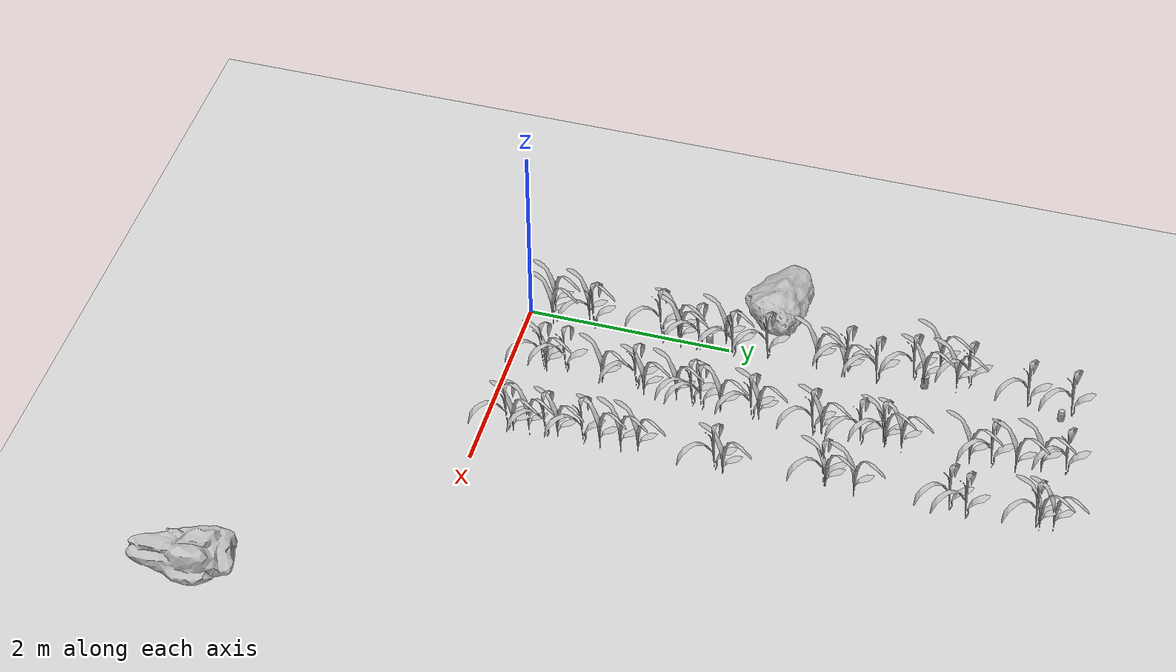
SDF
<sdf version="1.7">
 <world name="default">
  <light name="sun" type="directional">
   <pose>0 0 10 0 -0 0</pose>
   <diffuse>0.8 0.8 0.8 1</diffuse>
   <specular>0.2 0.2 0.2 1</specular>
   <attenuation>
    <range>1000</range>
    <constant>0.9</constant>
    <linear>0.01</linear>
    <quadratic>0.001</quadratic>
   </attenuation>
   <direction>-0.5 0.1 -0.9</direction>
   <spot><inner_angle>0</inner_angle><outer_angle>0</outer_angle><falloff>0</falloff></spot>
  </light>
  <model name="ground_plane">
   <static>1</static>
   <link name="link">
    <collision name="collision">
     <geometry><plane><normal>0 0 1</normal><size>100 100</size></plane></geometry>
     <surface>
      <contact><collide_bitmask>65535</collide_bitmask></contact>
      <friction><ode><mu>100</mu><mu2>50</mu2></ode></friction>
     </surface>
    </collision>
    <visual name="visual">
     <cast_shadows>0</cast_shadows>
     <geometry><plane><normal>0 0 1</normal><size>100 100</size></plane></geometry>
     <material>
      <script><uri>file://media/materials/scripts/gazebo.material</uri><name>Gazebo/Grey</name></script>
     </material>
    </visual>
   </link>
  </model>
  <gravity>0 0 -9.8</gravity>
  <magnetic_field>6e-06 2.3e-05 -4.2e-05</magnetic_field>
  <atmosphere type="adiabatic"/>
  <physics type="ode">
   <max_step_size>0.001</max_step_size>
   <real_time_factor>1</real_time_factor>
   <real_time_update_rate>1000</real_time_update_rate>
  </physics>
  <scene><ambient>0.4 0.4 0.4 1</ambient><background>0.7 0.7 0.7 1</background><shadows>1</shadows></scene>
  <audio><device>default</device></audio>
  <spherical_coordinates>
   <surface_model>EARTH_WGS84</surface_model>
   <latitude_deg>0</latitude_deg>
   <longitude_deg>0</longitude_deg>
   <elevation>0</elevation>
   <heading_deg>0</heading_deg>
  </spherical_coordinates>
  <model name="maize_01">
   <static>0</static>
   <pose>0.049824 3.46854 -0 0 -2e-06 0.000121</pose>
   <link name="maize_01_link">
    <inertial>
     <pose>0 0 0.01 0 -0 0</pose>
     <mass>0.3</mass>
     <inertia>
      <ixx>0.00334167</ixx>
      <ixy>0</ixy>
      <ixz>0</ixz>
      <iyy>0.00334167</iyy>
      <iyz>0</iyz>
      <izz>1.66667e-05</izz>
     </inertia>
     <pose>0 0 0.1 0 -0 0</pose>
    </inertial>
    <collision name="collision">
     <pose>0 0 0.2 0 -0 0</pose>
     <geometry><box><size>0.02 0.02 0.4</size></box></geometry>
     <surface><friction><ode><mu>10</mu><mu2>10</mu2></ode></friction></surface>
    </collision>
    <visual name="visual">
     <geometry>
      <mesh><uri>model://maize_01/meshes/maize_01.dae</uri><scale>0.683166 0.683166 0.683166</scale></mesh>
     </geometry>
    </visual>
   </link>
  </model>
  <model name="maize_02">
   <static>0</static>
   <pose>0.111758 3.16505 -0 0 -3e-06 7.7e-05</pose>
   <link name="maize_02_link">
    <inertial>
     <pose>0 0 0.01 0 -0 0</pose>
     <mass>0.3</mass>
     <inertia>
      <ixx>0.00334167</ixx>
      <ixy>0</ixy>
      <ixz>0</ixz>
      <iyy>0.00334167</iyy>
      <iyz>0</iyz>
      <izz>1.66667e-05</izz>
     </inertia>
     <pose>0 0 0.1 0 -0 0</pose>
    </inertial>
    <collision name="collision">
     <pose>0 0 0.2 0 -0 0</pose>
     <geometry><box><size>0.02 0.02 0.4</size></box></geometry>
     <surface><friction><ode><mu>10</mu><mu2>10</mu2></ode></friction></surface>
    </collision>
    <visual name="visual">
     <geometry>
      <mesh><uri>model://maize_02/meshes/maize_02.dae</uri><scale>0.683166 0.683166 0.683166</scale></mesh>
     </geometry>
    </visual>
   </link>
  </model>
  <model name="maize_01_0">
   <static>0</static>
   <pose>-0.015999 3.17206 1e-06 2e-05 -3.1e-05 -0.000122</pose>
   <link name="maize_01_link">
    <inertial>
     <pose>0 0 0.01 0 -0 0</pose>
     <mass>0.3</mass>
     <inertia>
      <ixx>0.00334167</ixx>
      <ixy>0</ixy>
      <ixz>0</ixz>
      <iyy>0.00334167</iyy>
      <iyz>0</iyz>
      <izz>1.66667e-05</izz>
     </inertia>
     <pose>0 0 0.1 0 -0 0</pose>
    </inertial>
    <collision name="collision">
     <pose>0 0 0.2 0 -0 0</pose>
     <geometry><box><size>0.02 0.02 0.4</size></box></geometry>
     <surface><friction><ode><mu>10</mu><mu2>10</mu2></ode></friction></surface>
    </collision>
    <visual name="visual">
     <geometry>
      <mesh><uri>model://maize_01/meshes/maize_01.dae</uri><scale>0.683166 0.683166 0.683166</scale></mesh>
     </geometry>
    </visual>
   </link>
  </model>
  <model name="maize_02_0">
   <static>0</static>
   <pose>0.042009 2.87635 -0 -4e-06 1.1e-05 4.1e-05</pose>
   <link name="maize_02_link">
    <inertial>
     <pose>0 0 0.01 0 -0 0</pose>
     <mass>0.3</mass>
     <inertia>
      <ixx>0.00334167</ixx>
      <ixy>0</ixy>
      <ixz>0</ixz>
      <iyy>0.00334167</iyy>
      <iyz>0</iyz>
      <izz>1.66667e-05</izz>
     </inertia>
     <pose>0 0 0.1 0 -0 0</pose>
    </inertial>
    <collision name="collision">
     <pose>0 0 0.2 0 -0 0</pose>
     <geometry><box><size>0.02 0.02 0.4</size></box></geometry>
     <surface><friction><ode><mu>10</mu><mu2>10</mu2></ode></friction></surface>
    </collision>
    <visual name="visual">
     <geometry>
      <mesh><uri>model://maize_02/meshes/maize_02.dae</uri><scale>0.683166 0.683166 0.683166</scale></mesh>
     </geometry>
    </visual>
   </link>
  </model>
  <model name="maize_01_1">
   <static>0</static>
   <pose>0.011051 2.38704 -1e-05 -2.3e-05 1e-06 9.6e-05</pose>
   <link name="maize_01_link">
    <inertial>
     <pose>0 0 0.01 0 -0 0</pose>
     <mass>0.3</mass>
     <inertia>
      <ixx>0.00334167</ixx>
      <ixy>0</ixy>
      <ixz>0</ixz>
      <iyy>0.00334167</iyy>
      <iyz>0</iyz>
      <izz>1.66667e-05</izz>
     </inertia>
     <pose>0 0 0.1 0 -0 0</pose>
    </inertial>
    <collision name="collision">
     <pose>0 0 0.2 0 -0 0</pose>
     <geometry><box><size>0.02 0.02 0.4</size></box></geometry>
     <surface><friction><ode><mu>10</mu><mu2>10</mu2></ode></friction></surface>
    </collision>
    <visual name="visual">
     <geometry>
      <mesh><uri>model://maize_01/meshes/maize_01.dae</uri><scale>0.683166 0.683166 0.683166</scale></mesh>
     </geometry>
    </visual>
   </link>
  </model>
  <model name="maize_01_2">
   <static>0</static>
   <pose>0.07497 2.06028 1e-06 4e-05 -2e-05 -7.9e-05</pose>
   <link name="maize_01_link">
    <inertial>
     <pose>0 0 0.01 0 -0 0</pose>
     <mass>0.3</mass>
     <inertia>
      <ixx>0.00334167</ixx>
      <ixy>0</ixy>
      <ixz>0</ixz>
      <iyy>0.00334167</iyy>
      <iyz>0</iyz>
      <izz>1.66667e-05</izz>
     </inertia>
     <pose>0 0 0.1 0 -0 0</pose>
    </inertial>
    <collision name="collision">
     <pose>0 0 0.2 0 -0 0</pose>
     <geometry><box><size>0.02 0.02 0.4</size></box></geometry>
     <surface><friction><ode><mu>10</mu><mu2>10</mu2></ode></friction></surface>
    </collision>
    <visual name="visual">
     <geometry>
      <mesh><uri>model://maize_01/meshes/maize_01.dae</uri><scale>0.683166 0.683166 0.683166</scale></mesh>
     </geometry>
    </visual>
   </link>
  </model>
  <model name="maize_02_1">
   <static>0</static>
   <pose>-0.016542 1.96877 -0 0 -2e-06 -3.7e-05</pose>
   <link name="maize_02_link">
    <inertial>
     <pose>0 0 0.01 0 -0 0</pose>
     <mass>0.3</mass>
     <inertia>
      <ixx>0.00334167</ixx>
      <ixy>0</ixy>
      <ixz>0</ixz>
      <iyy>0.00334167</iyy>
      <iyz>0</iyz>
      <izz>1.66667e-05</izz>
     </inertia>
     <pose>0 0 0.1 0 -0 0</pose>
    </inertial>
    <collision name="collision">
     <pose>0 0 0.2 0 -0 0</pose>
     <geometry><box><size>0.02 0.02 0.4</size></box></geometry>
     <surface><friction><ode><mu>10</mu><mu2>10</mu2></ode></friction></surface>
    </collision>
    <visual name="visual">
     <geometry>
      <mesh><uri>model://maize_02/meshes/maize_02.dae</uri><scale>0.683166 0.683166 0.683166</scale></mesh>
     </geometry>
    </visual>
   </link>
  </model>
  <model name="maize_02_2">
   <static>0</static>
   <pose>0.105617 1.54652 -0 1.4e-05 -1.2e-05 5.1e-05</pose>
   <link name="maize_02_link">
    <inertial>
     <pose>0 0 0.01 0 -0 0</pose>
     <mass>0.3</mass>
     <inertia>
      <ixx>0.00334167</ixx>
      <ixy>0</ixy>
      <ixz>0</ixz>
      <iyy>0.00334167</iyy>
      <iyz>0</iyz>
      <izz>1.66667e-05</izz>
     </inertia>
     <pose>0 0 0.1 0 -0 0</pose>
    </inertial>
    <collision name="collision">
     <pose>0 0 0.2 0 -0 0</pose>
     <geometry><box><size>0.02 0.02 0.4</size></box></geometry>
     <surface><friction><ode><mu>10</mu><mu2>10</mu2></ode></friction></surface>
    </collision>
    <visual name="visual">
     <geometry>
      <mesh><uri>model://maize_02/meshes/maize_02.dae</uri><scale>0.683166 0.683166 0.683166</scale></mesh>
     </geometry>
    </visual>
   </link>
  </model>
  <model name="maize_01_3">
   <static>0</static>
   <pose>-0.015504 1.32268 -0 -3e-06 -0 4.7e-05</pose>
   <link name="maize_01_link">
    <inertial>
     <pose>0 0 0.01 0 -0 0</pose>
     <mass>0.3</mass>
     <inertia>
      <ixx>0.00334167</ixx>
      <ixy>0</ixy>
      <ixz>0</ixz>
      <iyy>0.00334167</iyy>
      <iyz>0</iyz>
      <izz>1.66667e-05</izz>
     </inertia>
     <pose>0 0 0.1 0 -0 0</pose>
    </inertial>
    <collision name="collision">
     <pose>0 0 0.2 0 -0 0</pose>
     <geometry><box><size>0.02 0.02 0.4</size></box></geometry>
     <surface><friction><ode><mu>10</mu><mu2>10</mu2></ode></friction></surface>
    </collision>
    <visual name="visual">
     <geometry>
      <mesh><uri>model://maize_01/meshes/maize_01.dae</uri><scale>0.683166 0.683166 0.683166</scale></mesh>
     </geometry>
    </visual>
   </link>
  </model>
  <model name="maize_02_3">
   <static>0</static>
   <pose>0.023357 1.49971 -0 0 1e-06 -5.6e-05</pose>
   <link name="maize_02_link">
    <inertial>
     <pose>0 0 0.01 0 -0 0</pose>
     <mass>0.3</mass>
     <inertia>
      <ixx>0.00334167</ixx>
      <ixy>0</ixy>
      <ixz>0</ixz>
      <iyy>0.00334167</iyy>
      <iyz>0</iyz>
      <izz>1.66667e-05</izz>
     </inertia>
     <pose>0 0 0.1 0 -0 0</pose>
    </inertial>
    <collision name="collision">
     <pose>0 0 0.2 0 -0 0</pose>
     <geometry><box><size>0.02 0.02 0.4</size></box></geometry>
     <surface><friction><ode><mu>10</mu><mu2>10</mu2></ode></friction></surface>
    </collision>
    <visual name="visual">
     <geometry>
      <mesh><uri>model://maize_02/meshes/maize_02.dae</uri><scale>0.683166 0.683166 0.683166</scale></mesh>
     </geometry>
    </visual>
   </link>
  </model>
  <model name="maize_01_4">
   <static>0</static>
   <pose>0.072572 0.67038 -0 0 3e-06 0.000162</pose>
   <link name="maize_01_link">
    <inertial>
     <pose>0 0 0.01 0 -0 0</pose>
     <mass>0.3</mass>
     <inertia>
      <ixx>0.00334167</ixx>
      <ixy>0</ixy>
      <ixz>0</ixz>
      <iyy>0.00334167</iyy>
      <iyz>0</iyz>
      <izz>1.66667e-05</izz>
     </inertia>
     <pose>0 0 0.1 0 -0 0</pose>
    </inertial>
    <collision name="collision">
     <pose>0 0 0.2 0 -0 0</pose>
     <geometry><box><size>0.02 0.02 0.4</size></box></geometry>
     <surface><friction><ode><mu>10</mu><mu2>10</mu2></ode></friction></surface>
    </collision>
    <visual name="visual">
     <geometry>
      <mesh><uri>model://maize_01/meshes/maize_01.dae</uri><scale>0.683166 0.683166 0.683166</scale></mesh>
     </geometry>
    </visual>
   </link>
  </model>
  <model name="maize_02_4">
   <static>0</static>
   <pose>-0.001208 0.596565 -0 0 -4e-06 -0.000126</pose>
   <link name="maize_02_link">
    <inertial>
     <pose>0 0 0.01 0 -0 0</pose>
     <mass>0.3</mass>
     <inertia>
      <ixx>0.00334167</ixx>
      <ixy>0</ixy>
      <ixz>0</ixz>
      <iyy>0.00334167</iyy>
      <iyz>0</iyz>
      <izz>1.66667e-05</izz>
     </inertia>
     <pose>0 0 0.1 0 -0 0</pose>
    </inertial>
    <collision name="collision">
     <pose>0 0 0.2 0 -0 0</pose>
     <geometry><box><size>0.02 0.02 0.4</size></box></geometry>
     <surface><friction><ode><mu>10</mu><mu2>10</mu2></ode></friction></surface>
    </collision>
    <visual name="visual">
     <geometry>
      <mesh><uri>model://maize_02/meshes/maize_02.dae</uri><scale>0.683166 0.683166 0.683166</scale></mesh>
     </geometry>
    </visual>
   </link>
  </model>
  <model name="maize_02_5">
   <static>0</static>
   <pose>0.131935 0.266044 -1e-06 1e-05 -4e-06 0.00012</pose>
   <link name="maize_02_link">
    <inertial>
     <pose>0 0 0.01 0 -0 0</pose>
     <mass>0.3</mass>
     <inertia>
      <ixx>0.00334167</ixx>
      <ixy>0</ixy>
      <ixz>0</ixz>
      <iyy>0.00334167</iyy>
      <iyz>0</iyz>
      <izz>1.66667e-05</izz>
     </inertia>
     <pose>0 0 0.1 0 -0 0</pose>
    </inertial>
    <collision name="collision">
     <pose>0 0 0.2 0 -0 0</pose>
     <geometry><box><size>0.02 0.02 0.4</size></box></geometry>
     <surface><friction><ode><mu>10</mu><mu2>10</mu2></ode></friction></surface>
    </collision>
    <visual name="visual">
     <geometry>
      <mesh><uri>model://maize_02/meshes/maize_02.dae</uri><scale>0.683166 0.683166 0.683166</scale></mesh>
     </geometry>
    </visual>
   </link>
  </model>
  <model name="maize_02_6">
   <static>0</static>
   <pose>-0.029944 0.244897 -9e-06 1.6e-05 -1e-06 0.000118</pose>
   <link name="maize_02_link">
    <inertial>
     <pose>0 0 0.01 0 -0 0</pose>
     <mass>0.3</mass>
     <inertia>
      <ixx>0.00334167</ixx>
      <ixy>0</ixy>
      <ixz>0</ixz>
      <iyy>0.00334167</iyy>
      <iyz>0</iyz>
      <izz>1.66667e-05</izz>
     </inertia>
     <pose>0 0 0.1 0 -0 0</pose>
    </inertial>
    <collision name="collision">
     <pose>0 0 0.2 0 -0 0</pose>
     <geometry><box><size>0.02 0.02 0.4</size></box></geometry>
     <surface><friction><ode><mu>10</mu><mu2>10</mu2></ode></friction></surface>
    </collision>
    <visual name="visual">
     <geometry>
      <mesh><uri>model://maize_02/meshes/maize_02.dae</uri><scale>0.683166 0.683166 0.683166</scale></mesh>
     </geometry>
    </visual>
   </link>
  </model>
  <model name="maize_01_5">
   <static>0</static>
   <pose>0.06978 1.72616 -9e-06 -5e-06 -2.3e-05 9.6e-05</pose>
   <link name="maize_01_link">
    <inertial>
     <pose>0 0 0.01 0 -0 0</pose>
     <mass>0.3</mass>
     <inertia>
      <ixx>0.00334167</ixx>
      <ixy>0</ixy>
      <ixz>0</ixz>
      <iyy>0.00334167</iyy>
      <iyz>0</iyz>
      <izz>1.66667e-05</izz>
     </inertia>
     <pose>0 0 0.1 0 -0 0</pose>
    </inertial>
    <collision name="collision">
     <pose>0 0 0.2 0 -0 0</pose>
     <geometry><box><size>0.02 0.02 0.4</size></box></geometry>
     <surface><friction><ode><mu>10</mu><mu2>10</mu2></ode></friction></surface>
    </collision>
    <visual name="visual">
     <geometry>
      <mesh><uri>model://maize_01/meshes/maize_01.dae</uri><scale>0.683166 0.683166 0.683166</scale></mesh>
     </geometry>
    </visual>
   </link>
  </model>
  <model name="maize_01_6">
   <static>0</static>
   <pose>-0.076784 3.80554 -0 -1e-06 0 -8.8e-05</pose>
   <link name="maize_01_link">
    <inertial>
     <pose>0 0 0.01 0 -0 0</pose>
     <mass>0.3</mass>
     <inertia>
      <ixx>0.00334167</ixx>
      <ixy>0</ixy>
      <ixz>0</ixz>
      <iyy>0.00334167</iyy>
      <iyz>0</iyz>
      <izz>1.66667e-05</izz>
     </inertia>
     <pose>0 0 0.1 0 -0 0</pose>
    </inertial>
    <collision name="collision">
     <pose>0 0 0.2 0 -0 0</pose>
     <geometry><box><size>0.02 0.02 0.4</size></box></geometry>
     <surface><friction><ode><mu>10</mu><mu2>10</mu2></ode></friction></surface>
    </collision>
    <visual name="visual">
     <geometry>
      <mesh><uri>model://maize_01/meshes/maize_01.dae</uri><scale>0.683166 0.683166 0.683166</scale></mesh>
     </geometry>
    </visual>
   </link>
  </model>
  <model name="maize_02_7">
   <static>0</static>
   <pose>0.000118 3.91355 -0 0 -1e-06 -0.010854</pose>
   <link name="maize_02_link">
    <inertial>
     <pose>0 0 0.01 0 -0 0</pose>
     <mass>0.3</mass>
     <inertia>
      <ixx>0.00334167</ixx>
      <ixy>0</ixy>
      <ixz>0</ixz>
      <iyy>0.00334167</iyy>
      <iyz>0</iyz>
      <izz>1.66667e-05</izz>
     </inertia>
     <pose>0 0 0.1 0 -0 0</pose>
    </inertial>
    <collision name="collision">
     <pose>0 0 0.2 0 -0 0</pose>
     <geometry><box><size>0.02 0.02 0.4</size></box></geometry>
     <surface><friction><ode><mu>10</mu><mu2>10</mu2></ode></friction></surface>
    </collision>
    <visual name="visual">
     <geometry>
      <mesh><uri>model://maize_02/meshes/maize_02.dae</uri><scale>0.683166 0.683166 0.683166</scale></mesh>
     </geometry>
    </visual>
   </link>
  </model>
  <model name="maize_02_8">
   <static>0</static>
   <pose>-0.243542 4.02964 -1e-05 -0 2.1e-05 6.4e-05</pose>
   <link name="maize_02_link">
    <inertial>
     <pose>0 0 0.01 0 -0 0</pose>
     <mass>0.3</mass>
     <inertia>
      <ixx>0.00334167</ixx>
      <ixy>0</ixy>
      <ixz>0</ixz>
      <iyy>0.00334167</iyy>
      <iyz>0</iyz>
      <izz>1.66667e-05</izz>
     </inertia>
     <pose>0 0 0.1 0 -0 0</pose>
    </inertial>
    <collision name="collision">
     <pose>0 0 0.2 0 -0 0</pose>
     <geometry><box><size>0.02 0.02 0.4</size></box></geometry>
     <surface><friction><ode><mu>10</mu><mu2>10</mu2></ode></friction></surface>
    </collision>
    <visual name="visual">
     <geometry>
      <mesh><uri>model://maize_02/meshes/maize_02.dae</uri><scale>0.683166 0.683166 0.683166</scale></mesh>
     </geometry>
    </visual>
   </link>
  </model>
  <model name="maize_02_9">
   <static>0</static>
   <pose>-0.032657 4.22394 -0 1e-06 -0 -0.000264</pose>
   <link name="maize_02_link">
    <inertial>
     <pose>0 0 0.01 0 -0 0</pose>
     <mass>0.3</mass>
     <inertia>
      <ixx>0.00334167</ixx>
      <ixy>0</ixy>
      <ixz>0</ixz>
      <iyy>0.00334167</iyy>
      <iyz>0</iyz>
      <izz>1.66667e-05</izz>
     </inertia>
     <pose>0 0 0.1 0 -0 0</pose>
    </inertial>
    <collision name="collision">
     <pose>0 0 0.2 0 -0 0</pose>
     <geometry><box><size>0.02 0.02 0.4</size></box></geometry>
     <surface><friction><ode><mu>10</mu><mu2>10</mu2></ode></friction></surface>
    </collision>
    <visual name="visual">
     <geometry>
      <mesh><uri>model://maize_02/meshes/maize_02.dae</uri><scale>0.683166 0.683166 0.683166</scale></mesh>
     </geometry>
    </visual>
   </link>
  </model>
  <model name="maize_01_7">
   <static>0</static>
   <pose>-0.119233 4.33145 -0 0 2e-06 -1.6e-05</pose>
   <link name="maize_01_link">
    <inertial>
     <pose>0 0 0.01 0 -0 0</pose>
     <mass>0.3</mass>
     <inertia>
      <ixx>0.00334167</ixx>
      <ixy>0</ixy>
      <ixz>0</ixz>
      <iyy>0.00334167</iyy>
      <iyz>0</iyz>
      <izz>1.66667e-05</izz>
     </inertia>
     <pose>0 0 0.1 0 -0 0</pose>
    </inertial>
    <collision name="collision">
     <pose>0 0 0.2 0 -0 0</pose>
     <geometry><box><size>0.02 0.02 0.4</size></box></geometry>
     <surface><friction><ode><mu>10</mu><mu2>10</mu2></ode></friction></surface>
    </collision>
    <visual name="visual">
     <geometry>
      <mesh><uri>model://maize_01/meshes/maize_01.dae</uri><scale>0.683166 0.683166 0.683166</scale></mesh>
     </geometry>
    </visual>
   </link>
  </model>
  <model name="maize_01_8">
   <static>0</static>
   <pose>-0.031178 4.91656 0 1.8e-05 -1.1e-05 -7.1e-05</pose>
   <link name="maize_01_link">
    <inertial>
     <pose>0 0 0.01 0 -0 0</pose>
     <mass>0.3</mass>
     <inertia>
      <ixx>0.00334167</ixx>
      <ixy>0</ixy>
      <ixz>0</ixz>
      <iyy>0.00334167</iyy>
      <iyz>0</iyz>
      <izz>1.66667e-05</izz>
     </inertia>
     <pose>0 0 0.1 0 -0 0</pose>
    </inertial>
    <collision name="collision">
     <pose>0 0 0.2 0 -0 0</pose>
     <geometry><box><size>0.02 0.02 0.4</size></box></geometry>
     <surface><friction><ode><mu>10</mu><mu2>10</mu2></ode></friction></surface>
    </collision>
    <visual name="visual">
     <geometry>
      <mesh><uri>model://maize_01/meshes/maize_01.dae</uri><scale>0.683166 0.683166 0.683166</scale></mesh>
     </geometry>
    </visual>
   </link>
  </model>
  <model name="maize_01_9">
   <static>0</static>
   <pose>-0.013724 5.3365 0 -3.3e-05 -1.6e-05 -3.9e-05</pose>
   <link name="maize_01_link">
    <inertial>
     <pose>0 0 0.01 0 -0 0</pose>
     <mass>0.3</mass>
     <inertia>
      <ixx>0.00334167</ixx>
      <ixy>0</ixy>
      <ixz>0</ixz>
      <iyy>0.00334167</iyy>
      <iyz>0</iyz>
      <izz>1.66667e-05</izz>
     </inertia>
     <pose>0 0 0.1 0 -0 0</pose>
    </inertial>
    <collision name="collision">
     <pose>0 0 0.2 0 -0 0</pose>
     <geometry><box><size>0.02 0.02 0.4</size></box></geometry>
     <surface><friction><ode><mu>10</mu><mu2>10</mu2></ode></friction></surface>
    </collision>
    <visual name="visual">
     <geometry>
      <mesh><uri>model://maize_01/meshes/maize_01.dae</uri><scale>0.683166 0.683166 0.683166</scale></mesh>
     </geometry>
    </visual>
   </link>
  </model>
  <model name="coke_can">
   <link name="link">
    <inertial>
     <mass>0.39</mass>
     <inertia>
      <ixx>0.00055575</ixx>
      <ixy>0</ixy>
      <ixz>0</ixz>
      <iyy>0.00055575</iyy>
      <iyz>0</iyz>
      <izz>0.0001755</izz>
     </inertia>
    </inertial>
    <collision name="collision">
     <pose>0 0 0.065 0 -0 0</pose>
     <geometry><box><size>0.05 0.05 0.12</size></box></geometry>
     <surface>
      <friction><ode><mu>1</mu><mu2>1</mu2></ode></friction>
      <contact><ode><kp>1e+07</kp><kd>1</kd><min_depth>0.001</min_depth><max_vel>0.1</max_vel></ode></contact>
     </surface>
    </collision>
    <visual name="visual">
     <pose>0.003937 0.004724 -0.18 0 -0 0</pose>
     <geometry><mesh><uri>model://coke_can/meshes/coke_can.dae</uri></mesh></geometry>
    </visual>
   </link>
   <pose>0.041157 5.2468 -0.006 0 -0 0</pose>
  </model>
  <model name="coke_can_0">
   <link name="link">
    <inertial>
     <mass>0.39</mass>
     <inertia>
      <ixx>0.00055575</ixx>
      <ixy>0</ixy>
      <ixz>0</ixz>
      <iyy>0.00055575</iyy>
      <iyz>0</iyz>
      <izz>0.0001755</izz>
     </inertia>
    </inertial>
    <collision name="collision">
     <pose>0 0 0.065 0 -0 0</pose>
     <geometry><box><size>0.05 0.05 0.12</size></box></geometry>
     <surface>
      <friction><ode><mu>1</mu><mu2>1</mu2></ode></friction>
      <contact><ode><kp>1e+07</kp><kd>1</kd><min_depth>0.001</min_depth><max_vel>0.1</max_vel></ode></contact>
     </surface>
    </collision>
    <visual name="visual">
     <pose>0.003937 0.004724 -0.18 0 -0 0</pose>
     <geometry><mesh><uri>model://coke_can/meshes/coke_can.dae</uri></mesh></geometry>
    </visual>
   </link>
   <pose>-0.038625 1.79987 -0.006 0 -0 0</pose>
  </model>
  <model name="beer">
   <link name="link">
    <inertial>
     <mass>0.39</mass>
     <inertia><ixx>0.00058</ixx><ixy>0</ixy><ixz>0</ixz><iyy>0.00058</iyy><iyz>0</iyz><izz>0.00019</izz></inertia>
    </inertial>
    <collision name="collision"><geometry><box><size>0.05 0.05 0.15</size></box></geometry></collision>
    <visual name="visual">
     <geometry><cylinder><radius>0.035</radius><length>0.15</length></cylinder></geometry>
     <material>
      <script>
       <uri>model://beer/materials/scripts</uri>
       <uri>model://beer/materials/textures</uri>
       <name>Beer/Diffuse</name>
      </script>
     </material>
    </visual>
   </link>
   <pose>-0.035525 3.91992 0.074999 3.6e-05 2.3e-05 -0.003499</pose>
  </model>
  <model name="Stone_01">
   <pose>-0.648652 2.32885 0.2 0 -0 0</pose>
   <static>0</static>
   <link name="Stone_01_link">
    <inertial>
     <mass>157</mass>
     <inertia>
      <ixx>0.013198</ixx>
      <ixy>7.1e-05</ixy>
      <ixz>-0.002737</ixz>
      <iyy>0.035595</iyy>
      <iyz>-0.000109</iyz>
      <izz>0.043366</izz>
     </inertia>
     <pose>0.026819 0.042579 -0.021161 0 -0 0</pose>
    </inertial>
    <collision name="collision">
     <geometry><box><size>1 0.642406 0.326631</size></box></geometry>
     <surface><friction><ode><mu>10</mu><mu2>10</mu2></ode></friction></surface>
    </collision>
    <visual name="visual">
     <geometry><mesh><uri>model://stone_01/meshes/stone_01.dae</uri><scale>1 1 1</scale></mesh></geometry>
     <material>
      <pbr>
       <metal>
        <albedo_map>model://stone_01/textures/stone_01.jpg</albedo_map>
        <ambient_occlusion_map>model://stone_01/textures/stone_01_occlusion.jpg</ambient_occlusion_map>
        <normal_map type="tangent">model://stone_01/textures/stone_01_normal.jpg</normal_map>
       </metal>
      </pbr>
     </material>
    </visual>
   </link>
  </model>
  <model name="Stone_02">
   <pose>3.91963 -2.0917 0.2 0 -0 0</pose>
   <static>0</static>
   <link name="Stone_02_link">
    <inertial>
     <mass>142</mass>
     <inertia>
      <ixx>0.003534</ixx>
      <ixy>0.000463</ixy>
      <ixz>0.000122</ixz>
      <iyy>0.001486</iyy>
      <iyz>-1.5e-05</iyz>
      <izz>0.004391</izz>
     </inertia>
     <pose>0.001732 0.073943 -0.017533 0 -0 0</pose>
    </inertial>
    <collision name="collision">
     <geometry><box><size>0.597647 1 0.299114</size></box></geometry>
     <surface><friction><ode><mu>10</mu><mu2>10</mu2></ode></friction></surface>
    </collision>
    <visual name="visual">
     <geometry><mesh><uri>model://stone_02/meshes/stone_02.dae</uri><scale>1 1 1</scale></mesh></geometry>
     <material>
      <pbr>
       <metal>
        <albedo_map>model://stone_02/textures/stone_02.jpg</albedo_map>
        <normal_map type="tangent">model://stone_02/textures/stone_02_normal.jpg</normal_map>
       </metal>
      </pbr>
     </material>
    </visual>
   </link>
  </model>
  <model name="maize_01_10">
   <static>0</static>
   <pose>0.724811 5.40268 -0 0 -2e-06 0.000193</pose>
   <link name="maize_01_link">
    <inertial>
     <pose>0 0 0.01 0 -0 0</pose>
     <mass>0.3</mass>
     <inertia>
      <ixx>0.00334167</ixx>
      <ixy>0</ixy>
      <ixz>0</ixz>
      <iyy>0.00334167</iyy>
      <iyz>0</iyz>
      <izz>1.66667e-05</izz>
     </inertia>
     <pose>0 0 0.1 0 -0 0</pose>
    </inertial>
    <collision name="collision">
     <pose>0 0 0.2 0 -0 0</pose>
     <geometry><box><size>0.02 0.02 0.4</size></box></geometry>
     <surface><friction><ode><mu>10</mu><mu2>10</mu2></ode></friction></surface>
    </collision>
    <visual name="visual">
     <geometry>
      <mesh><uri>model://maize_01/meshes/maize_01.dae</uri><scale>0.683166 0.683166 0.683166</scale></mesh>
     </geometry>
    </visual>
   </link>
  </model>
  <model name="maize_02_10">
   <static>0</static>
   <pose>0.776544 5.17782 0 -3e-06 -1.6e-05 0.000123</pose>
   <link name="maize_02_link">
    <inertial>
     <pose>0 0 0.01 0 -0 0</pose>
     <mass>0.3</mass>
     <inertia>
      <ixx>0.00334167</ixx>
      <ixy>0</ixy>
      <ixz>0</ixz>
      <iyy>0.00334167</iyy>
      <iyz>0</iyz>
      <izz>1.66667e-05</izz>
     </inertia>
     <pose>0 0 0.1 0 -0 0</pose>
    </inertial>
    <collision name="collision">
     <pose>0 0 0.2 0 -0 0</pose>
     <geometry><box><size>0.02 0.02 0.4</size></box></geometry>
     <surface><friction><ode><mu>10</mu><mu2>10</mu2></ode></friction></surface>
    </collision>
    <visual name="visual">
     <geometry>
      <mesh><uri>model://maize_02/meshes/maize_02.dae</uri><scale>0.683166 0.683166 0.683166</scale></mesh>
     </geometry>
    </visual>
   </link>
  </model>
  <model name="maize_02_11">
   <static>0</static>
   <pose>0.84916 4.94849 -0 3e-06 -0 7e-06</pose>
   <link name="maize_02_link">
    <inertial>
     <pose>0 0 0.01 0 -0 0</pose>
     <mass>0.3</mass>
     <inertia>
      <ixx>0.00334167</ixx>
      <ixy>0</ixy>
      <ixz>0</ixz>
      <iyy>0.00334167</iyy>
      <iyz>0</iyz>
      <izz>1.66667e-05</izz>
     </inertia>
     <pose>0 0 0.1 0 -0 0</pose>
    </inertial>
    <collision name="collision">
     <pose>0 0 0.2 0 -0 0</pose>
     <geometry><box><size>0.02 0.02 0.4</size></box></geometry>
     <surface><friction><ode><mu>10</mu><mu2>10</mu2></ode></friction></surface>
    </collision>
    <visual name="visual">
     <geometry>
      <mesh><uri>model://maize_02/meshes/maize_02.dae</uri><scale>0.683166 0.683166 0.683166</scale></mesh>
     </geometry>
    </visual>
   </link>
  </model>
  <model name="maize_01_11">
   <static>0</static>
   <pose>0.821763 4.71955 -0 0 3e-06 8.1e-05</pose>
   <link name="maize_01_link">
    <inertial>
     <pose>0 0 0.01 0 -0 0</pose>
     <mass>0.3</mass>
     <inertia>
      <ixx>0.00334167</ixx>
      <ixy>0</ixy>
      <ixz>0</ixz>
      <iyy>0.00334167</iyy>
      <iyz>0</iyz>
      <izz>1.66667e-05</izz>
     </inertia>
     <pose>0 0 0.1 0 -0 0</pose>
    </inertial>
    <collision name="collision">
     <pose>0 0 0.2 0 -0 0</pose>
     <geometry><box><size>0.02 0.02 0.4</size></box></geometry>
     <surface><friction><ode><mu>10</mu><mu2>10</mu2></ode></friction></surface>
    </collision>
    <visual name="visual">
     <geometry>
      <mesh><uri>model://maize_01/meshes/maize_01.dae</uri><scale>0.683166 0.683166 0.683166</scale></mesh>
     </geometry>
    </visual>
   </link>
  </model>
  <model name="maize_02_12">
   <static>0</static>
   <pose>0.856995 4.51664 1e-06 -2e-05 4.2e-05 -5.3e-05</pose>
   <link name="maize_02_link">
    <inertial>
     <pose>0 0 0.01 0 -0 0</pose>
     <mass>0.3</mass>
     <inertia>
      <ixx>0.00334167</ixx>
      <ixy>0</ixy>
      <ixz>0</ixz>
      <iyy>0.00334167</iyy>
      <iyz>0</iyz>
      <izz>1.66667e-05</izz>
     </inertia>
     <pose>0 0 0.1 0 -0 0</pose>
    </inertial>
    <collision name="collision">
     <pose>0 0 0.2 0 -0 0</pose>
     <geometry><box><size>0.02 0.02 0.4</size></box></geometry>
     <surface><friction><ode><mu>10</mu><mu2>10</mu2></ode></friction></surface>
    </collision>
    <visual name="visual">
     <geometry>
      <mesh><uri>model://maize_02/meshes/maize_02.dae</uri><scale>0.683166 0.683166 0.683166</scale></mesh>
     </geometry>
    </visual>
   </link>
  </model>
  <model name="maize_02_13">
   <static>0</static>
   <pose>0.868163 3.87583 -0 -3e-06 -0 -1.8e-05</pose>
   <link name="maize_02_link">
    <inertial>
     <pose>0 0 0.01 0 -0 0</pose>
     <mass>0.3</mass>
     <inertia>
      <ixx>0.00334167</ixx>
      <ixy>0</ixy>
      <ixz>0</ixz>
      <iyy>0.00334167</iyy>
      <iyz>0</iyz>
      <izz>1.66667e-05</izz>
     </inertia>
     <pose>0 0 0.1 0 -0 0</pose>
    </inertial>
    <collision name="collision">
     <pose>0 0 0.2 0 -0 0</pose>
     <geometry><box><size>0.02 0.02 0.4</size></box></geometry>
     <surface><friction><ode><mu>10</mu><mu2>10</mu2></ode></friction></surface>
    </collision>
    <visual name="visual">
     <geometry>
      <mesh><uri>model://maize_02/meshes/maize_02.dae</uri><scale>0.683166 0.683166 0.683166</scale></mesh>
     </geometry>
    </visual>
   </link>
  </model>
  <model name="maize_02_14">
   <static>0</static>
   <pose>0.872322 3.71669 -0 3e-06 -0 -1.7e-05</pose>
   <link name="maize_02_link">
    <inertial>
     <pose>0 0 0.01 0 -0 0</pose>
     <mass>0.3</mass>
     <inertia>
      <ixx>0.00334167</ixx>
      <ixy>0</ixy>
      <ixz>0</ixz>
      <iyy>0.00334167</iyy>
      <iyz>0</iyz>
      <izz>1.66667e-05</izz>
     </inertia>
     <pose>0 0 0.1 0 -0 0</pose>
    </inertial>
    <collision name="collision">
     <pose>0 0 0.2 0 -0 0</pose>
     <geometry><box><size>0.02 0.02 0.4</size></box></geometry>
     <surface><friction><ode><mu>10</mu><mu2>10</mu2></ode></friction></surface>
    </collision>
    <visual name="visual">
     <geometry>
      <mesh><uri>model://maize_02/meshes/maize_02.dae</uri><scale>0.683166 0.683166 0.683166</scale></mesh>
     </geometry>
    </visual>
   </link>
  </model>
  <model name="maize_01_12">
   <static>0</static>
   <pose>0.840863 3.70277 0 -6.7e-05 -2e-06 -0.000145</pose>
   <link name="maize_01_link">
    <inertial>
     <pose>0 0 0.01 0 -0 0</pose>
     <mass>0.3</mass>
     <inertia>
      <ixx>0.00334167</ixx>
      <ixy>0</ixy>
      <ixz>0</ixz>
      <iyy>0.00334167</iyy>
      <iyz>0</iyz>
      <izz>1.66667e-05</izz>
     </inertia>
     <pose>0 0 0.1 0 -0 0</pose>
    </inertial>
    <collision name="collision">
     <pose>0 0 0.2 0 -0 0</pose>
     <geometry><box><size>0.02 0.02 0.4</size></box></geometry>
     <surface><friction><ode><mu>10</mu><mu2>10</mu2></ode></friction></surface>
    </collision>
    <visual name="visual">
     <geometry>
      <mesh><uri>model://maize_01/meshes/maize_01.dae</uri><scale>0.683166 0.683166 0.683166</scale></mesh>
     </geometry>
    </visual>
   </link>
  </model>
  <model name="maize_01_13">
   <static>0</static>
   <pose>0.870665 3.48909 0 -1e-05 -2.2e-05 -8.9e-05</pose>
   <link name="maize_01_link">
    <inertial>
     <pose>0 0 0.01 0 -0 0</pose>
     <mass>0.3</mass>
     <inertia>
      <ixx>0.00334167</ixx>
      <ixy>0</ixy>
      <ixz>0</ixz>
      <iyy>0.00334167</iyy>
      <iyz>0</iyz>
      <izz>1.66667e-05</izz>
     </inertia>
     <pose>0 0 0.1 0 -0 0</pose>
    </inertial>
    <collision name="collision">
     <pose>0 0 0.2 0 -0 0</pose>
     <geometry><box><size>0.02 0.02 0.4</size></box></geometry>
     <surface><friction><ode><mu>10</mu><mu2>10</mu2></ode></friction></surface>
    </collision>
    <visual name="visual">
     <geometry>
      <mesh><uri>model://maize_01/meshes/maize_01.dae</uri><scale>0.683166 0.683166 0.683166</scale></mesh>
     </geometry>
    </visual>
   </link>
  </model>
  <model name="maize_02_15">
   <static>0</static>
   <pose>0.900619 3.11772 -0 1e-06 0 2.6e-05</pose>
   <link name="maize_02_link">
    <inertial>
     <pose>0 0 0.01 0 -0 0</pose>
     <mass>0.3</mass>
     <inertia>
      <ixx>0.00334167</ixx>
      <ixy>0</ixy>
      <ixz>0</ixz>
      <iyy>0.00334167</iyy>
      <iyz>0</iyz>
      <izz>1.66667e-05</izz>
     </inertia>
     <pose>0 0 0.1 0 -0 0</pose>
    </inertial>
    <collision name="collision">
     <pose>0 0 0.2 0 -0 0</pose>
     <geometry><box><size>0.02 0.02 0.4</size></box></geometry>
     <surface><friction><ode><mu>10</mu><mu2>10</mu2></ode></friction></surface>
    </collision>
    <visual name="visual">
     <geometry>
      <mesh><uri>model://maize_02/meshes/maize_02.dae</uri><scale>0.683166 0.683166 0.683166</scale></mesh>
     </geometry>
    </visual>
   </link>
  </model>
  <model name="maize_01_14">
   <static>0</static>
   <pose>0.868465 3.02958 -0 0 -3e-06 9.4e-05</pose>
   <link name="maize_01_link">
    <inertial>
     <pose>0 0 0.01 0 -0 0</pose>
     <mass>0.3</mass>
     <inertia>
      <ixx>0.00334167</ixx>
      <ixy>0</ixy>
      <ixz>0</ixz>
      <iyy>0.00334167</iyy>
      <iyz>0</iyz>
      <izz>1.66667e-05</izz>
     </inertia>
     <pose>0 0 0.1 0 -0 0</pose>
    </inertial>
    <collision name="collision">
     <pose>0 0 0.2 0 -0 0</pose>
     <geometry><box><size>0.02 0.02 0.4</size></box></geometry>
     <surface><friction><ode><mu>10</mu><mu2>10</mu2></ode></friction></surface>
    </collision>
    <visual name="visual">
     <geometry>
      <mesh><uri>model://maize_01/meshes/maize_01.dae</uri><scale>0.683166 0.683166 0.683166</scale></mesh>
     </geometry>
    </visual>
   </link>
  </model>
  <model name="maize_02_16">
   <static>0</static>
   <pose>0.854904 2.50047 0 0 1.2e-05 -4.2e-05</pose>
   <link name="maize_02_link">
    <inertial>
     <pose>0 0 0.01 0 -0 0</pose>
     <mass>0.3</mass>
     <inertia>
      <ixx>0.00334167</ixx>
      <ixy>0</ixy>
      <ixz>0</ixz>
      <iyy>0.00334167</iyy>
      <iyz>0</iyz>
      <izz>1.66667e-05</izz>
     </inertia>
     <pose>0 0 0.1 0 -0 0</pose>
    </inertial>
    <collision name="collision">
     <pose>0 0 0.2 0 -0 0</pose>
     <geometry><box><size>0.02 0.02 0.4</size></box></geometry>
     <surface><friction><ode><mu>10</mu><mu2>10</mu2></ode></friction></surface>
    </collision>
    <visual name="visual">
     <geometry>
      <mesh><uri>model://maize_02/meshes/maize_02.dae</uri><scale>0.683166 0.683166 0.683166</scale></mesh>
     </geometry>
    </visual>
   </link>
  </model>
  <model name="maize_02_17">
   <static>0</static>
   <pose>0.871532 2.13424 -0 1.2e-05 -1e-05 8.5e-05</pose>
   <link name="maize_02_link">
    <inertial>
     <pose>0 0 0.01 0 -0 0</pose>
     <mass>0.3</mass>
     <inertia>
      <ixx>0.00334167</ixx>
      <ixy>0</ixy>
      <ixz>0</ixz>
      <iyy>0.00334167</iyy>
      <iyz>0</iyz>
      <izz>1.66667e-05</izz>
     </inertia>
     <pose>0 0 0.1 0 -0 0</pose>
    </inertial>
    <collision name="collision">
     <pose>0 0 0.2 0 -0 0</pose>
     <geometry><box><size>0.02 0.02 0.4</size></box></geometry>
     <surface><friction><ode><mu>10</mu><mu2>10</mu2></ode></friction></surface>
    </collision>
    <visual name="visual">
     <geometry>
      <mesh><uri>model://maize_02/meshes/maize_02.dae</uri><scale>0.683166 0.683166 0.683166</scale></mesh>
     </geometry>
    </visual>
   </link>
  </model>
  <model name="maize_01_15">
   <static>0</static>
   <pose>0.837841 2.43256 -0 3e-06 0 3.9e-05</pose>
   <link name="maize_01_link">
    <inertial>
     <pose>0 0 0.01 0 -0 0</pose>
     <mass>0.3</mass>
     <inertia>
      <ixx>0.00334167</ixx>
      <ixy>0</ixy>
      <ixz>0</ixz>
      <iyy>0.00334167</iyy>
      <iyz>0</iyz>
      <izz>1.66667e-05</izz>
     </inertia>
     <pose>0 0 0.1 0 -0 0</pose>
    </inertial>
    <collision name="collision">
     <pose>0 0 0.2 0 -0 0</pose>
     <geometry><box><size>0.02 0.02 0.4</size></box></geometry>
     <surface><friction><ode><mu>10</mu><mu2>10</mu2></ode></friction></surface>
    </collision>
    <visual name="visual">
     <geometry>
      <mesh><uri>model://maize_01/meshes/maize_01.dae</uri><scale>0.683166 0.683166 0.683166</scale></mesh>
     </geometry>
    </visual>
   </link>
  </model>
  <model name="maize_01_16">
   <static>0</static>
   <pose>0.845044 1.94362 0 -0 -0 -2.3e-05</pose>
   <link name="maize_01_link">
    <inertial>
     <pose>0 0 0.01 0 -0 0</pose>
     <mass>0.3</mass>
     <inertia>
      <ixx>0.00334167</ixx>
      <ixy>0</ixy>
      <ixz>0</ixz>
      <iyy>0.00334167</iyy>
      <iyz>0</iyz>
      <izz>1.66667e-05</izz>
     </inertia>
     <pose>0 0 0.1 0 -0 0</pose>
    </inertial>
    <collision name="collision">
     <pose>0 0 0.2 0 -0 0</pose>
     <geometry><box><size>0.02 0.02 0.4</size></box></geometry>
     <surface><friction><ode><mu>10</mu><mu2>10</mu2></ode></friction></surface>
    </collision>
    <visual name="visual">
     <geometry>
      <mesh><uri>model://maize_01/meshes/maize_01.dae</uri><scale>0.683166 0.683166 0.683166</scale></mesh>
     </geometry>
    </visual>
   </link>
  </model>
  <model name="maize_01_17">
   <static>0</static>
   <pose>0.813423 1.8453 -1e-05 9e-06 -0 3.1e-05</pose>
   <link name="maize_01_link">
    <inertial>
     <pose>0 0 0.01 0 -0 0</pose>
     <mass>0.3</mass>
     <inertia>
      <ixx>0.00334167</ixx>
      <ixy>0</ixy>
      <ixz>0</ixz>
      <iyy>0.00334167</iyy>
      <iyz>0</iyz>
      <izz>1.66667e-05</izz>
     </inertia>
     <pose>0 0 0.1 0 -0 0</pose>
    </inertial>
    <collision name="collision">
     <pose>0 0 0.2 0 -0 0</pose>
     <geometry><box><size>0.02 0.02 0.4</size></box></geometry>
     <surface><friction><ode><mu>10</mu><mu2>10</mu2></ode></friction></surface>
    </collision>
    <visual name="visual">
     <geometry>
      <mesh><uri>model://maize_01/meshes/maize_01.dae</uri><scale>0.683166 0.683166 0.683166</scale></mesh>
     </geometry>
    </visual>
   </link>
  </model>
  <model name="maize_02_18">
   <static>0</static>
   <pose>0.815557 1.68966 0 -4e-06 7.2e-05 2.4e-05</pose>
   <link name="maize_02_link">
    <inertial>
     <pose>0 0 0.01 0 -0 0</pose>
     <mass>0.3</mass>
     <inertia>
      <ixx>0.00334167</ixx>
      <ixy>0</ixy>
      <ixz>0</ixz>
      <iyy>0.00334167</iyy>
      <iyz>0</iyz>
      <izz>1.66667e-05</izz>
     </inertia>
     <pose>0 0 0.1 0 -0 0</pose>
    </inertial>
    <collision name="collision">
     <pose>0 0 0.2 0 -0 0</pose>
     <geometry><box><size>0.02 0.02 0.4</size></box></geometry>
     <surface><friction><ode><mu>10</mu><mu2>10</mu2></ode></friction></surface>
    </collision>
    <visual name="visual">
     <geometry>
      <mesh><uri>model://maize_02/meshes/maize_02.dae</uri><scale>0.683166 0.683166 0.683166</scale></mesh>
     </geometry>
    </visual>
   </link>
  </model>
  <model name="maize_02_19">
   <static>0</static>
   <pose>0.845031 1.3783 -0 0 -4e-06 -9.7e-05</pose>
   <link name="maize_02_link">
    <inertial>
     <pose>0 0 0.01 0 -0 0</pose>
     <mass>0.3</mass>
     <inertia>
      <ixx>0.00334167</ixx>
      <ixy>0</ixy>
      <ixz>0</ixz>
      <iyy>0.00334167</iyy>
      <iyz>0</iyz>
      <izz>1.66667e-05</izz>
     </inertia>
     <pose>0 0 0.1 0 -0 0</pose>
    </inertial>
    <collision name="collision">
     <pose>0 0 0.2 0 -0 0</pose>
     <geometry><box><size>0.02 0.02 0.4</size></box></geometry>
     <surface><friction><ode><mu>10</mu><mu2>10</mu2></ode></friction></surface>
    </collision>
    <visual name="visual">
     <geometry>
      <mesh><uri>model://maize_02/meshes/maize_02.dae</uri><scale>0.683166 0.683166 0.683166</scale></mesh>
     </geometry>
    </visual>
   </link>
  </model>
  <model name="maize_01_18">
   <static>0</static>
   <pose>0.752388 1.28292 1e-06 -8.3e-05 -1e-06 0.000104</pose>
   <link name="maize_01_link">
    <inertial>
     <pose>0 0 0.01 0 -0 0</pose>
     <mass>0.3</mass>
     <inertia>
      <ixx>0.00334167</ixx>
      <ixy>0</ixy>
      <ixz>0</ixz>
      <iyy>0.00334167</iyy>
      <iyz>0</iyz>
      <izz>1.66667e-05</izz>
     </inertia>
     <pose>0 0 0.1 0 -0 0</pose>
    </inertial>
    <collision name="collision">
     <pose>0 0 0.2 0 -0 0</pose>
     <geometry><box><size>0.02 0.02 0.4</size></box></geometry>
     <surface><friction><ode><mu>10</mu><mu2>10</mu2></ode></friction></surface>
    </collision>
    <visual name="visual">
     <geometry>
      <mesh><uri>model://maize_01/meshes/maize_01.dae</uri><scale>0.683166 0.683166 0.683166</scale></mesh>
     </geometry>
    </visual>
   </link>
  </model>
  <model name="maize_02_20">
   <static>0</static>
   <pose>0.811056 0.959733 -0 -4e-06 -0 -9e-05</pose>
   <link name="maize_02_link">
    <inertial>
     <pose>0 0 0.01 0 -0 0</pose>
     <mass>0.3</mass>
     <inertia>
      <ixx>0.00334167</ixx>
      <ixy>0</ixy>
      <ixz>0</ixz>
      <iyy>0.00334167</iyy>
      <iyz>0</iyz>
      <izz>1.66667e-05</izz>
     </inertia>
     <pose>0 0 0.1 0 -0 0</pose>
    </inertial>
    <collision name="collision">
     <pose>0 0 0.2 0 -0 0</pose>
     <geometry><box><size>0.02 0.02 0.4</size></box></geometry>
     <surface><friction><ode><mu>10</mu><mu2>10</mu2></ode></friction></surface>
    </collision>
    <visual name="visual">
     <geometry>
      <mesh><uri>model://maize_02/meshes/maize_02.dae</uri><scale>0.683166 0.683166 0.683166</scale></mesh>
     </geometry>
    </visual>
   </link>
  </model>
  <model name="maize_02_21">
   <static>0</static>
   <pose>0.784947 0.394703 -0 -1e-05 -4e-06 8e-05</pose>
   <link name="maize_02_link">
    <inertial>
     <pose>0 0 0.01 0 -0 0</pose>
     <mass>0.3</mass>
     <inertia>
      <ixx>0.00334167</ixx>
      <ixy>0</ixy>
      <ixz>0</ixz>
      <iyy>0.00334167</iyy>
      <iyz>0</iyz>
      <izz>1.66667e-05</izz>
     </inertia>
     <pose>0 0 0.1 0 -0 0</pose>
    </inertial>
    <collision name="collision">
     <pose>0 0 0.2 0 -0 0</pose>
     <geometry><box><size>0.02 0.02 0.4</size></box></geometry>
     <surface><friction><ode><mu>10</mu><mu2>10</mu2></ode></friction></surface>
    </collision>
    <visual name="visual">
     <geometry>
      <mesh><uri>model://maize_02/meshes/maize_02.dae</uri><scale>0.683166 0.683166 0.683166</scale></mesh>
     </geometry>
    </visual>
   </link>
  </model>
  <model name="maize_01_19">
   <static>0</static>
   <pose>0.721958 0.348489 -0 -4e-06 -0 4e-06</pose>
   <link name="maize_01_link">
    <inertial>
     <pose>0 0 0.01 0 -0 0</pose>
     <mass>0.3</mass>
     <inertia>
      <ixx>0.00334167</ixx>
      <ixy>0</ixy>
      <ixz>0</ixz>
      <iyy>0.00334167</iyy>
      <iyz>0</iyz>
      <izz>1.66667e-05</izz>
     </inertia>
     <pose>0 0 0.1 0 -0 0</pose>
    </inertial>
    <collision name="collision">
     <pose>0 0 0.2 0 -0 0</pose>
     <geometry><box><size>0.02 0.02 0.4</size></box></geometry>
     <surface><friction><ode><mu>10</mu><mu2>10</mu2></ode></friction></surface>
    </collision>
    <visual name="visual">
     <geometry>
      <mesh><uri>model://maize_01/meshes/maize_01.dae</uri><scale>0.683166 0.683166 0.683166</scale></mesh>
     </geometry>
    </visual>
   </link>
  </model>
  <model name="maize_01_20">
   <static>0</static>
   <pose>0.711205 0.57024 -0 -0 2e-06 4e-06</pose>
   <link name="maize_01_link">
    <inertial>
     <pose>0 0 0.01 0 -0 0</pose>
     <mass>0.3</mass>
     <inertia>
      <ixx>0.00334167</ixx>
      <ixy>0</ixy>
      <ixz>0</ixz>
      <iyy>0.00334167</iyy>
      <iyz>0</iyz>
      <izz>1.66667e-05</izz>
     </inertia>
     <pose>0 0 0.1 0 -0 0</pose>
    </inertial>
    <collision name="collision">
     <pose>0 0 0.2 0 -0 0</pose>
     <geometry><box><size>0.02 0.02 0.4</size></box></geometry>
     <surface><friction><ode><mu>10</mu><mu2>10</mu2></ode></friction></surface>
    </collision>
    <visual name="visual">
     <geometry>
      <mesh><uri>model://maize_01/meshes/maize_01.dae</uri><scale>0.683166 0.683166 0.683166</scale></mesh>
     </geometry>
    </visual>
   </link>
  </model>
  <model name="maize_01_21">
   <static>0</static>
   <pose>1.57174 0.252303 -1e-06 -8e-06 -4e-06 2.1e-05</pose>
   <link name="maize_01_link">
    <inertial>
     <pose>0 0 0.01 0 -0 0</pose>
     <mass>0.3</mass>
     <inertia>
      <ixx>0.00334167</ixx>
      <ixy>0</ixy>
      <ixz>0</ixz>
      <iyy>0.00334167</iyy>
      <iyz>0</iyz>
      <izz>1.66667e-05</izz>
     </inertia>
     <pose>0 0 0.1 0 -0 0</pose>
    </inertial>
    <collision name="collision">
     <pose>0 0 0.2 0 -0 0</pose>
     <geometry><box><size>0.02 0.02 0.4</size></box></geometry>
     <surface><friction><ode><mu>10</mu><mu2>10</mu2></ode></friction></surface>
    </collision>
    <visual name="visual">
     <geometry>
      <mesh><uri>model://maize_01/meshes/maize_01.dae</uri><scale>0.683166 0.683166 0.683166</scale></mesh>
     </geometry>
    </visual>
   </link>
  </model>
  <model name="maize_02_22">
   <static>0</static>
   <pose>1.63323 0.324722 -0 2e-06 -0 2.3e-05</pose>
   <link name="maize_02_link">
    <inertial>
     <pose>0 0 0.01 0 -0 0</pose>
     <mass>0.3</mass>
     <inertia>
      <ixx>0.00334167</ixx>
      <ixy>0</ixy>
      <ixz>0</ixz>
      <iyy>0.00334167</iyy>
      <iyz>0</iyz>
      <izz>1.66667e-05</izz>
     </inertia>
     <pose>0 0 0.1 0 -0 0</pose>
    </inertial>
    <collision name="collision">
     <pose>0 0 0.2 0 -0 0</pose>
     <geometry><box><size>0.02 0.02 0.4</size></box></geometry>
     <surface><friction><ode><mu>10</mu><mu2>10</mu2></ode></friction></surface>
    </collision>
    <visual name="visual">
     <geometry>
      <mesh><uri>model://maize_02/meshes/maize_02.dae</uri><scale>0.683166 0.683166 0.683166</scale></mesh>
     </geometry>
    </visual>
   </link>
  </model>
  <model name="maize_02_23">
   <static>0</static>
   <pose>1.58833 0.46473 -0 -9e-06 2.2e-05 7.7e-05</pose>
   <link name="maize_02_link">
    <inertial>
     <pose>0 0 0.01 0 -0 0</pose>
     <mass>0.3</mass>
     <inertia>
      <ixx>0.00334167</ixx>
      <ixy>0</ixy>
      <ixz>0</ixz>
      <iyy>0.00334167</iyy>
      <iyz>0</iyz>
      <izz>1.66667e-05</izz>
     </inertia>
     <pose>0 0 0.1 0 -0 0</pose>
    </inertial>
    <collision name="collision">
     <pose>0 0 0.2 0 -0 0</pose>
     <geometry><box><size>0.02 0.02 0.4</size></box></geometry>
     <surface><friction><ode><mu>10</mu><mu2>10</mu2></ode></friction></surface>
    </collision>
    <visual name="visual">
     <geometry>
      <mesh><uri>model://maize_02/meshes/maize_02.dae</uri><scale>0.683166 0.683166 0.683166</scale></mesh>
     </geometry>
    </visual>
   </link>
  </model>
  <model name="maize_01_22">
   <static>0</static>
   <pose>1.57425 0.627197 0 2e-06 3.5e-05 1.4e-05</pose>
   <link name="maize_01_link">
    <inertial>
     <pose>0 0 0.01 0 -0 0</pose>
     <mass>0.3</mass>
     <inertia>
      <ixx>0.00334167</ixx>
      <ixy>0</ixy>
      <ixz>0</ixz>
      <iyy>0.00334167</iyy>
      <iyz>0</iyz>
      <izz>1.66667e-05</izz>
     </inertia>
     <pose>0 0 0.1 0 -0 0</pose>
    </inertial>
    <collision name="collision">
     <pose>0 0 0.2 0 -0 0</pose>
     <geometry><box><size>0.02 0.02 0.4</size></box></geometry>
     <surface><friction><ode><mu>10</mu><mu2>10</mu2></ode></friction></surface>
    </collision>
    <visual name="visual">
     <geometry>
      <mesh><uri>model://maize_01/meshes/maize_01.dae</uri><scale>0.683166 0.683166 0.683166</scale></mesh>
     </geometry>
    </visual>
   </link>
  </model>
  <model name="maize_02_24">
   <static>0</static>
   <pose>1.5971 0.749602 -9e-06 -7e-06 -4.9e-05 -1e-05</pose>
   <link name="maize_02_link">
    <inertial>
     <pose>0 0 0.01 0 -0 0</pose>
     <mass>0.3</mass>
     <inertia>
      <ixx>0.00334167</ixx>
      <ixy>0</ixy>
      <ixz>0</ixz>
      <iyy>0.00334167</iyy>
      <iyz>0</iyz>
      <izz>1.66667e-05</izz>
     </inertia>
     <pose>0 0 0.1 0 -0 0</pose>
    </inertial>
    <collision name="collision">
     <pose>0 0 0.2 0 -0 0</pose>
     <geometry><box><size>0.02 0.02 0.4</size></box></geometry>
     <surface><friction><ode><mu>10</mu><mu2>10</mu2></ode></friction></surface>
    </collision>
    <visual name="visual">
     <geometry>
      <mesh><uri>model://maize_02/meshes/maize_02.dae</uri><scale>0.683166 0.683166 0.683166</scale></mesh>
     </geometry>
    </visual>
   </link>
  </model>
  <model name="maize_01_23">
   <static>0</static>
   <pose>1.5479 0.982451 -0 0 -1e-06 1.5e-05</pose>
   <link name="maize_01_link">
    <inertial>
     <pose>0 0 0.01 0 -0 0</pose>
     <mass>0.3</mass>
     <inertia>
      <ixx>0.00334167</ixx>
      <ixy>0</ixy>
      <ixz>0</ixz>
      <iyy>0.00334167</iyy>
      <iyz>0</iyz>
      <izz>1.66667e-05</izz>
     </inertia>
     <pose>0 0 0.1 0 -0 0</pose>
    </inertial>
    <collision name="collision">
     <pose>0 0 0.2 0 -0 0</pose>
     <geometry><box><size>0.02 0.02 0.4</size></box></geometry>
     <surface><friction><ode><mu>10</mu><mu2>10</mu2></ode></friction></surface>
    </collision>
    <visual name="visual">
     <geometry>
      <mesh><uri>model://maize_01/meshes/maize_01.dae</uri><scale>0.683166 0.683166 0.683166</scale></mesh>
     </geometry>
    </visual>
   </link>
  </model>
  <model name="maize_02_25">
   <static>0</static>
   <pose>1.57961 1.15183 -0 4e-06 -0 5.3e-05</pose>
   <link name="maize_02_link">
    <inertial>
     <pose>0 0 0.01 0 -0 0</pose>
     <mass>0.3</mass>
     <inertia>
      <ixx>0.00334167</ixx>
      <ixy>0</ixy>
      <ixz>0</ixz>
      <iyy>0.00334167</iyy>
      <iyz>0</iyz>
      <izz>1.66667e-05</izz>
     </inertia>
     <pose>0 0 0.1 0 -0 0</pose>
    </inertial>
    <collision name="collision">
     <pose>0 0 0.2 0 -0 0</pose>
     <geometry><box><size>0.02 0.02 0.4</size></box></geometry>
     <surface><friction><ode><mu>10</mu><mu2>10</mu2></ode></friction></surface>
    </collision>
    <visual name="visual">
     <geometry>
      <mesh><uri>model://maize_02/meshes/maize_02.dae</uri><scale>0.683166 0.683166 0.683166</scale></mesh>
     </geometry>
    </visual>
   </link>
  </model>
  <model name="maize_02_26">
   <static>0</static>
   <pose>1.56519 1.34875 -0 -0 4e-06 5.6e-05</pose>
   <link name="maize_02_link">
    <inertial>
     <pose>0 0 0.01 0 -0 0</pose>
     <mass>0.3</mass>
     <inertia>
      <ixx>0.00334167</ixx>
      <ixy>0</ixy>
      <ixz>0</ixz>
      <iyy>0.00334167</iyy>
      <iyz>0</iyz>
      <izz>1.66667e-05</izz>
     </inertia>
     <pose>0 0 0.1 0 -0 0</pose>
    </inertial>
    <collision name="collision">
     <pose>0 0 0.2 0 -0 0</pose>
     <geometry><box><size>0.02 0.02 0.4</size></box></geometry>
     <surface><friction><ode><mu>10</mu><mu2>10</mu2></ode></friction></surface>
    </collision>
    <visual name="visual">
     <geometry>
      <mesh><uri>model://maize_02/meshes/maize_02.dae</uri><scale>0.683166 0.683166 0.683166</scale></mesh>
     </geometry>
    </visual>
   </link>
  </model>
  <model name="maize_02_27">
   <static>0</static>
   <pose>1.5617 1.51707 0 -4e-06 -0 6.1e-05</pose>
   <link name="maize_02_link">
    <inertial>
     <pose>0 0 0.01 0 -0 0</pose>
     <mass>0.3</mass>
     <inertia>
      <ixx>0.00334167</ixx>
      <ixy>0</ixy>
      <ixz>0</ixz>
      <iyy>0.00334167</iyy>
      <iyz>0</iyz>
      <izz>1.66667e-05</izz>
     </inertia>
     <pose>0 0 0.1 0 -0 0</pose>
    </inertial>
    <collision name="collision">
     <pose>0 0 0.2 0 -0 0</pose>
     <geometry><box><size>0.02 0.02 0.4</size></box></geometry>
     <surface><friction><ode><mu>10</mu><mu2>10</mu2></ode></friction></surface>
    </collision>
    <visual name="visual">
     <geometry>
      <mesh><uri>model://maize_02/meshes/maize_02.dae</uri><scale>0.683166 0.683166 0.683166</scale></mesh>
     </geometry>
    </visual>
   </link>
  </model>
  <model name="maize_01_24">
   <static>0</static>
   <pose>1.55313 2.25146 -0 2.5e-05 -4e-06 2.8e-05</pose>
   <link name="maize_01_link">
    <inertial>
     <pose>0 0 0.01 0 -0 0</pose>
     <mass>0.3</mass>
     <inertia>
      <ixx>0.00334167</ixx>
      <ixy>0</ixy>
      <ixz>0</ixz>
      <iyy>0.00334167</iyy>
      <iyz>0</iyz>
      <izz>1.66667e-05</izz>
     </inertia>
     <pose>0 0 0.1 0 -0 0</pose>
    </inertial>
    <collision name="collision">
     <pose>0 0 0.2 0 -0 0</pose>
     <geometry><box><size>0.02 0.02 0.4</size></box></geometry>
     <surface><friction><ode><mu>10</mu><mu2>10</mu2></ode></friction></surface>
    </collision>
    <visual name="visual">
     <geometry>
      <mesh><uri>model://maize_01/meshes/maize_01.dae</uri><scale>0.683166 0.683166 0.683166</scale></mesh>
     </geometry>
    </visual>
   </link>
  </model>
  <model name="maize_02_28">
   <static>0</static>
   <pose>1.62722 2.34663 -0 0 2e-06 4.9e-05</pose>
   <link name="maize_02_link">
    <inertial>
     <pose>0 0 0.01 0 -0 0</pose>
     <mass>0.3</mass>
     <inertia>
      <ixx>0.00334167</ixx>
      <ixy>0</ixy>
      <ixz>0</ixz>
      <iyy>0.00334167</iyy>
      <iyz>0</iyz>
      <izz>1.66667e-05</izz>
     </inertia>
     <pose>0 0 0.1 0 -0 0</pose>
    </inertial>
    <collision name="collision">
     <pose>0 0 0.2 0 -0 0</pose>
     <geometry><box><size>0.02 0.02 0.4</size></box></geometry>
     <surface><friction><ode><mu>10</mu><mu2>10</mu2></ode></friction></surface>
    </collision>
    <visual name="visual">
     <geometry>
      <mesh><uri>model://maize_02/meshes/maize_02.dae</uri><scale>0.683166 0.683166 0.683166</scale></mesh>
     </geometry>
    </visual>
   </link>
  </model>
  <model name="maize_01_25">
   <static>0</static>
   <pose>1.46312 3.26689 -0 0 -1e-06 1.5e-05</pose>
   <link name="maize_01_link">
    <inertial>
     <pose>0 0 0.01 0 -0 0</pose>
     <mass>0.3</mass>
     <inertia>
      <ixx>0.00334167</ixx>
      <ixy>0</ixy>
      <ixz>0</ixz>
      <iyy>0.00334167</iyy>
      <iyz>0</iyz>
      <izz>1.66667e-05</izz>
     </inertia>
     <pose>0 0 0.1 0 -0 0</pose>
    </inertial>
    <collision name="collision">
     <pose>0 0 0.2 0 -0 0</pose>
     <geometry><box><size>0.02 0.02 0.4</size></box></geometry>
     <surface><friction><ode><mu>10</mu><mu2>10</mu2></ode></friction></surface>
    </collision>
    <visual name="visual">
     <geometry>
      <mesh><uri>model://maize_01/meshes/maize_01.dae</uri><scale>0.683166 0.683166 0.683166</scale></mesh>
     </geometry>
    </visual>
   </link>
  </model>
  <model name="maize_02_29">
   <static>0</static>
   <pose>1.52625 3.29351 0 2e-06 1.8e-05 4.8e-05</pose>
   <link name="maize_02_link">
    <inertial>
     <pose>0 0 0.01 0 -0 0</pose>
     <mass>0.3</mass>
     <inertia>
      <ixx>0.00334167</ixx>
      <ixy>0</ixy>
      <ixz>0</ixz>
      <iyy>0.00334167</iyy>
      <iyz>0</iyz>
      <izz>1.66667e-05</izz>
     </inertia>
     <pose>0 0 0.1 0 -0 0</pose>
    </inertial>
    <collision name="collision">
     <pose>0 0 0.2 0 -0 0</pose>
     <geometry><box><size>0.02 0.02 0.4</size></box></geometry>
     <surface><friction><ode><mu>10</mu><mu2>10</mu2></ode></friction></surface>
    </collision>
    <visual name="visual">
     <geometry>
      <mesh><uri>model://maize_02/meshes/maize_02.dae</uri><scale>0.683166 0.683166 0.683166</scale></mesh>
     </geometry>
    </visual>
   </link>
  </model>
  <model name="maize_02_30">
   <static>0</static>
   <pose>1.53057 3.56459 1e-06 8e-06 -4.9e-05 1.9e-05</pose>
   <link name="maize_02_link">
    <inertial>
     <pose>0 0 0.01 0 -0 0</pose>
     <mass>0.3</mass>
     <inertia>
      <ixx>0.00334167</ixx>
      <ixy>0</ixy>
      <ixz>0</ixz>
      <iyy>0.00334167</iyy>
      <iyz>0</iyz>
      <izz>1.66667e-05</izz>
     </inertia>
     <pose>0 0 0.1 0 -0 0</pose>
    </inertial>
    <collision name="collision">
     <pose>0 0 0.2 0 -0 0</pose>
     <geometry><box><size>0.02 0.02 0.4</size></box></geometry>
     <surface><friction><ode><mu>10</mu><mu2>10</mu2></ode></friction></surface>
    </collision>
    <visual name="visual">
     <geometry>
      <mesh><uri>model://maize_02/meshes/maize_02.dae</uri><scale>0.683166 0.683166 0.683166</scale></mesh>
     </geometry>
    </visual>
   </link>
  </model>
  <model name="maize_01_26">
   <static>0</static>
   <pose>1.44827 4.44465 -0 0 3e-06 1e-05</pose>
   <link name="maize_01_link">
    <inertial>
     <pose>0 0 0.01 0 -0 0</pose>
     <mass>0.3</mass>
     <inertia>
      <ixx>0.00334167</ixx>
      <ixy>0</ixy>
      <ixz>0</ixz>
      <iyy>0.00334167</iyy>
      <iyz>0</iyz>
      <izz>1.66667e-05</izz>
     </inertia>
     <pose>0 0 0.1 0 -0 0</pose>
    </inertial>
    <collision name="collision">
     <pose>0 0 0.2 0 -0 0</pose>
     <geometry><box><size>0.02 0.02 0.4</size></box></geometry>
     <surface><friction><ode><mu>10</mu><mu2>10</mu2></ode></friction></surface>
    </collision>
    <visual name="visual">
     <geometry>
      <mesh><uri>model://maize_01/meshes/maize_01.dae</uri><scale>0.683166 0.683166 0.683166</scale></mesh>
     </geometry>
    </visual>
   </link>
  </model>
  <model name="maize_01_27">
   <static>0</static>
   <pose>1.50297 4.60712 0 7e-06 -4.2e-05 4.5e-05</pose>
   <link name="maize_01_link">
    <inertial>
     <pose>0 0 0.01 0 -0 0</pose>
     <mass>0.3</mass>
     <inertia>
      <ixx>0.00334167</ixx>
      <ixy>0</ixy>
      <ixz>0</ixz>
      <iyy>0.00334167</iyy>
      <iyz>0</iyz>
      <izz>1.66667e-05</izz>
     </inertia>
     <pose>0 0 0.1 0 -0 0</pose>
    </inertial>
    <collision name="collision">
     <pose>0 0 0.2 0 -0 0</pose>
     <geometry><box><size>0.02 0.02 0.4</size></box></geometry>
     <surface><friction><ode><mu>10</mu><mu2>10</mu2></ode></friction></surface>
    </collision>
    <visual name="visual">
     <geometry>
      <mesh><uri>model://maize_01/meshes/maize_01.dae</uri><scale>0.683166 0.683166 0.683166</scale></mesh>
     </geometry>
    </visual>
   </link>
  </model>
  <model name="maize_01_28">
   <static>0</static>
   <pose>1.43552 5.24636 -0 0 -0 2.1e-05</pose>
   <link name="maize_01_link">
    <inertial>
     <pose>0 0 0.01 0 -0 0</pose>
     <mass>0.3</mass>
     <inertia>
      <ixx>0.00334167</ixx>
      <ixy>0</ixy>
      <ixz>0</ixz>
      <iyy>0.00334167</iyy>
      <iyz>0</iyz>
      <izz>1.66667e-05</izz>
     </inertia>
     <pose>0 0 0.1 0 -0 0</pose>
    </inertial>
    <collision name="collision">
     <pose>0 0 0.2 0 -0 0</pose>
     <geometry><box><size>0.02 0.02 0.4</size></box></geometry>
     <surface><friction><ode><mu>10</mu><mu2>10</mu2></ode></friction></surface>
    </collision>
    <visual name="visual">
     <geometry>
      <mesh><uri>model://maize_01/meshes/maize_01.dae</uri><scale>0.683166 0.683166 0.683166</scale></mesh>
     </geometry>
    </visual>
   </link>
  </model>
  <model name="maize_02_31">
   <static>0</static>
   <pose>1.47616 5.28003 0 0 -2e-06 3.1e-05</pose>
   <link name="maize_02_link">
    <inertial>
     <pose>0 0 0.01 0 -0 0</pose>
     <mass>0.3</mass>
     <inertia>
      <ixx>0.00334167</ixx>
      <ixy>0</ixy>
      <ixz>0</ixz>
      <iyy>0.00334167</iyy>
      <iyz>0</iyz>
      <izz>1.66667e-05</izz>
     </inertia>
     <pose>0 0 0.1 0 -0 0</pose>
    </inertial>
    <collision name="collision">
     <pose>0 0 0.2 0 -0 0</pose>
     <geometry><box><size>0.02 0.02 0.4</size></box></geometry>
     <surface><friction><ode><mu>10</mu><mu2>10</mu2></ode></friction></surface>
    </collision>
    <visual name="visual">
     <geometry>
      <mesh><uri>model://maize_02/meshes/maize_02.dae</uri><scale>0.683166 0.683166 0.683166</scale></mesh>
     </geometry>
    </visual>
   </link>
  </model>
  <model name="maize_02_32">
   <static>0</static>
   <pose>1.45822 5.40415 0 0 -0 3.2e-05</pose>
   <link name="maize_02_link">
    <inertial>
     <pose>0 0 0.01 0 -0 0</pose>
     <mass>0.3</mass>
     <inertia>
      <ixx>0.00334167</ixx>
      <ixy>0</ixy>
      <ixz>0</ixz>
      <iyy>0.00334167</iyy>
      <iyz>0</iyz>
      <izz>1.66667e-05</izz>
     </inertia>
     <pose>0 0 0.1 0 -0 0</pose>
    </inertial>
    <collision name="collision">
     <pose>0 0 0.2 0 -0 0</pose>
     <geometry><box><size>0.02 0.02 0.4</size></box></geometry>
     <surface><friction><ode><mu>10</mu><mu2>10</mu2></ode></friction></surface>
    </collision>
    <visual name="visual">
     <geometry>
      <mesh><uri>model://maize_02/meshes/maize_02.dae</uri><scale>0.683166 0.683166 0.683166</scale></mesh>
     </geometry>
    </visual>
   </link>
  </model>
 </world>
</sdf>
